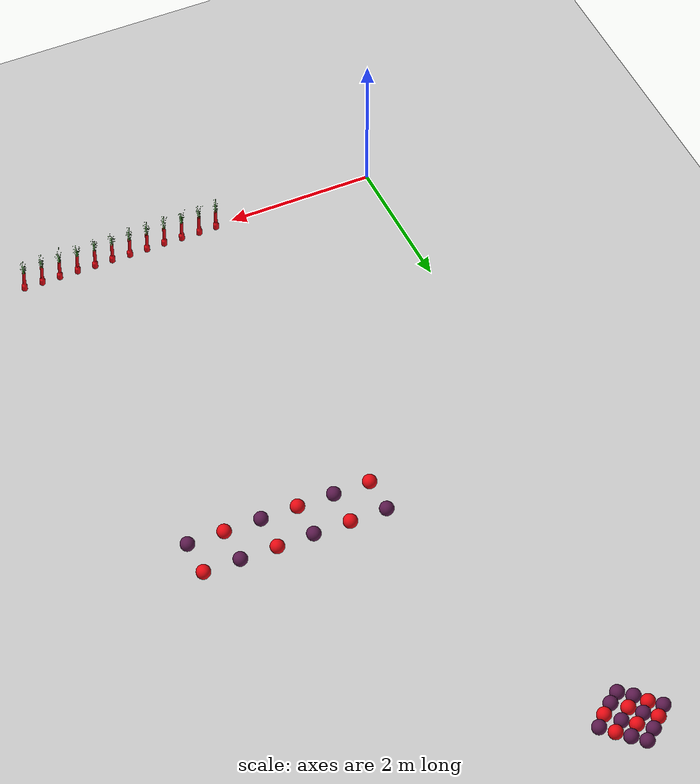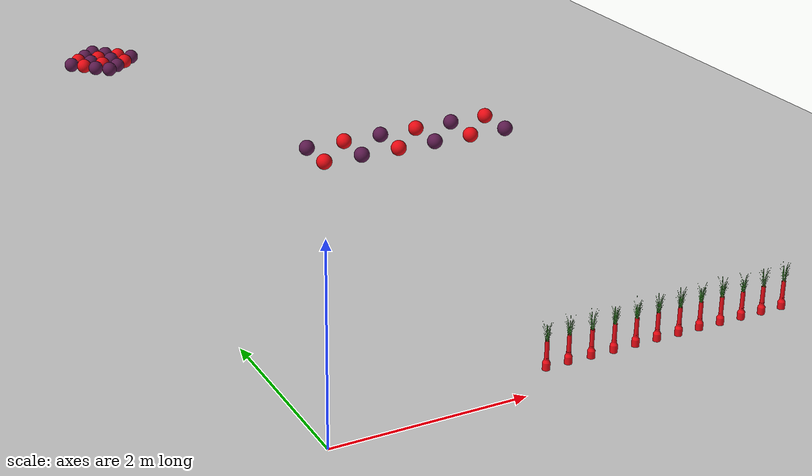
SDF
<sdf version="1.7">
 <world name="default">
  <light name="sun" type="directional">
   <pose>0 0 10 0 -0 0</pose>
   <diffuse>0.8 0.8 0.8 1</diffuse>
   <specular>0.2 0.2 0.2 1</specular>
   <attenuation>
    <range>1000</range>
    <constant>0.9</constant>
    <linear>0.01</linear>
    <quadratic>0.001</quadratic>
   </attenuation>
   <direction>-0.5 0.1 -0.9</direction>
   <spot><inner_angle>0</inner_angle><outer_angle>0</outer_angle><falloff>0</falloff></spot>
  </light>
  <model name="ground_plane">
   <static>1</static>
   <link name="link">
    <collision name="collision">
     <geometry><plane><normal>0 0 1</normal><size>100 100</size></plane></geometry>
     <surface>
      <contact><collide_bitmask>65535</collide_bitmask></contact>
      <friction><ode><mu>100</mu><mu2>50</mu2></ode></friction>
     </surface>
    </collision>
    <visual name="visual">
     <cast_shadows>0</cast_shadows>
     <geometry><plane><normal>0 0 1</normal><size>100 100</size></plane></geometry>
     <material>
      <script><uri>file://media/materials/scripts/gazebo.material</uri><name>Gazebo/Grey</name></script>
     </material>
    </visual>
   </link>
  </model>
  <gravity>0 0 -9.8</gravity>
  <magnetic_field>6e-06 2.3e-05 -4.2e-05</magnetic_field>
  <atmosphere type="adiabatic"/>
  <physics type="ode">
   <max_step_size>0.001</max_step_size>
   <real_time_factor>1</real_time_factor>
   <real_time_update_rate>1000</real_time_update_rate>
  </physics>
  <scene><ambient>0.4 0.4 0.4 1</ambient><background>0.7 0.7 0.7 1</background><shadows>1</shadows></scene>
  <audio><device>default</device></audio>
  <spherical_coordinates>
   <surface_model>EARTH_WGS84</surface_model>
   <latitude_deg>0</latitude_deg>
   <longitude_deg>0</longitude_deg>
   <elevation>0</elevation>
   <heading_deg>0</heading_deg>
  </spherical_coordinates>
  <model name="seed_red">
   <link name="link_1">
    <inertial>
     <mass>1</mass>
     <inertia>
      <ixx>0.166667</ixx>
      <ixy>0</ixy>
      <ixz>0</ixz>
      <iyy>0.166667</iyy>
      <iyz>0</iyz>
      <izz>0.166667</izz>
     </inertia>
    </inertial>
    <visual name="visual">
     <geometry>
      <mesh><uri>/home/entity014/abu2024_ws/src/abu_description/worlds/seed_red.dae</uri><scale>1 1 1</scale></mesh>
     </geometry>
    </visual>
    <collision name="collision">
     <geometry>
      <mesh><uri>/home/entity014/abu2024_ws/src/abu_description/worlds/seed_red.dae</uri><scale>1 1 1</scale></mesh>
     </geometry>
     <surface>
      <friction>
       <ode><mu>1</mu><mu2>1</mu2><fdir1>0 0 0</fdir1><slip1>0</slip1><slip2>0</slip2></ode>
       <torsional>
        <coefficient>1</coefficient>
        <patch_radius>0</patch_radius>
        <surface_radius>0</surface_radius>
        <use_patch_radius>1</use_patch_radius>
        <ode><slip>0</slip></ode>
       </torsional>
      </friction>
      <bounce><restitution_coefficient>0</restitution_coefficient><threshold>1e+06</threshold></bounce>
      <contact>
       <collide_without_contact>0</collide_without_contact>
       <collide_without_contact_bitmask>1</collide_without_contact_bitmask>
       <collide_bitmask>1</collide_bitmask>
       <ode>
        <soft_cfm>0</soft_cfm>
        <soft_erp>0.2</soft_erp>
        <kp>1e+13</kp>
        <kd>1</kd>
        <max_vel>0.01</max_vel>
        <min_depth>0</min_depth>
       </ode>
       <bullet>
        <split_impulse>1</split_impulse>
        <split_impulse_penetration_threshold>-0.01</split_impulse_penetration_threshold>
        <soft_cfm>0</soft_cfm>
        <soft_erp>0.2</soft_erp>
        <kp>1e+13</kp>
        <kd>1</kd>
       </bullet>
      </contact>
     </surface>
    </collision>
   </link>
   <static>0</static>
   <pose>2.30597 0.160395 0.24437 1e-05 -6e-06 -0.006182</pose>
  </model>
  <model name="seed_red_0">
   <link name="link_1">
    <inertial>
     <mass>1</mass>
     <inertia>
      <ixx>0.166667</ixx>
      <ixy>0</ixy>
      <ixz>0</ixz>
      <iyy>0.166667</iyy>
      <iyz>0</iyz>
      <izz>0.166667</izz>
     </inertia>
    </inertial>
    <visual name="visual">
     <geometry>
      <mesh><uri>/home/entity014/abu2024_ws/src/abu_description/worlds/seed_red.dae</uri><scale>1 1 1</scale></mesh>
     </geometry>
    </visual>
    <collision name="collision">
     <geometry>
      <mesh><uri>/home/entity014/abu2024_ws/src/abu_description/worlds/seed_red.dae</uri><scale>1 1 1</scale></mesh>
     </geometry>
     <surface>
      <friction>
       <ode><mu>1</mu><mu2>1</mu2><fdir1>0 0 0</fdir1><slip1>0</slip1><slip2>0</slip2></ode>
       <torsional>
        <coefficient>1</coefficient>
        <patch_radius>0</patch_radius>
        <surface_radius>0</surface_radius>
        <use_patch_radius>1</use_patch_radius>
        <ode><slip>0</slip></ode>
       </torsional>
      </friction>
      <bounce><restitution_coefficient>0</restitution_coefficient><threshold>1e+06</threshold></bounce>
      <contact>
       <collide_without_contact>0</collide_without_contact>
       <collide_without_contact_bitmask>1</collide_without_contact_bitmask>
       <collide_bitmask>1</collide_bitmask>
       <ode>
        <soft_cfm>0</soft_cfm>
        <soft_erp>0.2</soft_erp>
        <kp>1e+13</kp>
        <kd>1</kd>
        <max_vel>0.01</max_vel>
        <min_depth>0</min_depth>
       </ode>
       <bullet>
        <split_impulse>1</split_impulse>
        <split_impulse_penetration_threshold>-0.01</split_impulse_penetration_threshold>
        <soft_cfm>0</soft_cfm>
        <soft_erp>0.2</soft_erp>
        <kp>1e+13</kp>
        <kd>1</kd>
       </bullet>
      </contact>
     </surface>
    </collision>
   </link>
   <static>0</static>
   <pose>2.55267 0.166548 0.244409 0.000556 0.00091 -1.28036</pose>
  </model>
  <model name="seed_red_1">
   <link name="link_1">
    <inertial>
     <mass>1</mass>
     <inertia>
      <ixx>0.166667</ixx>
      <ixy>0</ixy>
      <ixz>0</ixz>
      <iyy>0.166667</iyy>
      <iyz>0</iyz>
      <izz>0.166667</izz>
     </inertia>
    </inertial>
    <visual name="visual">
     <geometry>
      <mesh><uri>/home/entity014/abu2024_ws/src/abu_description/worlds/seed_red.dae</uri><scale>1 1 1</scale></mesh>
     </geometry>
    </visual>
    <collision name="collision">
     <geometry>
      <mesh><uri>/home/entity014/abu2024_ws/src/abu_description/worlds/seed_red.dae</uri><scale>1 1 1</scale></mesh>
     </geometry>
     <surface>
      <friction>
       <ode><mu>1</mu><mu2>1</mu2><fdir1>0 0 0</fdir1><slip1>0</slip1><slip2>0</slip2></ode>
       <torsional>
        <coefficient>1</coefficient>
        <patch_radius>0</patch_radius>
        <surface_radius>0</surface_radius>
        <use_patch_radius>1</use_patch_radius>
        <ode><slip>0</slip></ode>
       </torsional>
      </friction>
      <bounce><restitution_coefficient>0</restitution_coefficient><threshold>1e+06</threshold></bounce>
      <contact>
       <collide_without_contact>0</collide_without_contact>
       <collide_without_contact_bitmask>1</collide_without_contact_bitmask>
       <collide_bitmask>1</collide_bitmask>
       <ode>
        <soft_cfm>0</soft_cfm>
        <soft_erp>0.2</soft_erp>
        <kp>1e+13</kp>
        <kd>1</kd>
        <max_vel>0.01</max_vel>
        <min_depth>0</min_depth>
       </ode>
       <bullet>
        <split_impulse>1</split_impulse>
        <split_impulse_penetration_threshold>-0.01</split_impulse_penetration_threshold>
        <soft_cfm>0</soft_cfm>
        <soft_erp>0.2</soft_erp>
        <kp>1e+13</kp>
        <kd>1</kd>
       </bullet>
      </contact>
     </surface>
    </collision>
   </link>
   <static>0</static>
   <pose>2.80489 0.16348 0.244359 4e-06 1e-06 0.181889</pose>
  </model>
  <model name="seed_red_2">
   <link name="link_1">
    <inertial>
     <mass>1</mass>
     <inertia>
      <ixx>0.166667</ixx>
      <ixy>0</ixy>
      <ixz>0</ixz>
      <iyy>0.166667</iyy>
      <iyz>0</iyz>
      <izz>0.166667</izz>
     </inertia>
    </inertial>
    <visual name="visual">
     <geometry>
      <mesh><uri>/home/entity014/abu2024_ws/src/abu_description/worlds/seed_red.dae</uri><scale>1 1 1</scale></mesh>
     </geometry>
    </visual>
    <collision name="collision">
     <geometry>
      <mesh><uri>/home/entity014/abu2024_ws/src/abu_description/worlds/seed_red.dae</uri><scale>1 1 1</scale></mesh>
     </geometry>
     <surface>
      <friction>
       <ode><mu>1</mu><mu2>1</mu2><fdir1>0 0 0</fdir1><slip1>0</slip1><slip2>0</slip2></ode>
       <torsional>
        <coefficient>1</coefficient>
        <patch_radius>0</patch_radius>
        <surface_radius>0</surface_radius>
        <use_patch_radius>1</use_patch_radius>
        <ode><slip>0</slip></ode>
       </torsional>
      </friction>
      <bounce><restitution_coefficient>0</restitution_coefficient><threshold>1e+06</threshold></bounce>
      <contact>
       <collide_without_contact>0</collide_without_contact>
       <collide_without_contact_bitmask>1</collide_without_contact_bitmask>
       <collide_bitmask>1</collide_bitmask>
       <ode>
        <soft_cfm>0</soft_cfm>
        <soft_erp>0.2</soft_erp>
        <kp>1e+13</kp>
        <kd>1</kd>
        <max_vel>0.01</max_vel>
        <min_depth>0</min_depth>
       </ode>
       <bullet>
        <split_impulse>1</split_impulse>
        <split_impulse_penetration_threshold>-0.01</split_impulse_penetration_threshold>
        <soft_cfm>0</soft_cfm>
        <soft_erp>0.2</soft_erp>
        <kp>1e+13</kp>
        <kd>1</kd>
       </bullet>
      </contact>
     </surface>
    </collision>
   </link>
   <static>0</static>
   <pose>3.05658 0.160248 0.244369 -0 -2e-06 0.02649</pose>
  </model>
  <model name="seed_red_3">
   <link name="link_1">
    <inertial>
     <mass>1</mass>
     <inertia>
      <ixx>0.166667</ixx>
      <ixy>0</ixy>
      <ixz>0</ixz>
      <iyy>0.166667</iyy>
      <iyz>0</iyz>
      <izz>0.166667</izz>
     </inertia>
    </inertial>
    <visual name="visual">
     <geometry>
      <mesh><uri>/home/entity014/abu2024_ws/src/abu_description/worlds/seed_red.dae</uri><scale>1 1 1</scale></mesh>
     </geometry>
    </visual>
    <collision name="collision">
     <geometry>
      <mesh><uri>/home/entity014/abu2024_ws/src/abu_description/worlds/seed_red.dae</uri><scale>1 1 1</scale></mesh>
     </geometry>
     <surface>
      <friction>
       <ode><mu>1</mu><mu2>1</mu2><fdir1>0 0 0</fdir1><slip1>0</slip1><slip2>0</slip2></ode>
       <torsional>
        <coefficient>1</coefficient>
        <patch_radius>0</patch_radius>
        <surface_radius>0</surface_radius>
        <use_patch_radius>1</use_patch_radius>
        <ode><slip>0</slip></ode>
       </torsional>
      </friction>
      <bounce><restitution_coefficient>0</restitution_coefficient><threshold>1e+06</threshold></bounce>
      <contact>
       <collide_without_contact>0</collide_without_contact>
       <collide_without_contact_bitmask>1</collide_without_contact_bitmask>
       <collide_bitmask>1</collide_bitmask>
       <ode>
        <soft_cfm>0</soft_cfm>
        <soft_erp>0.2</soft_erp>
        <kp>1e+13</kp>
        <kd>1</kd>
        <max_vel>0.01</max_vel>
        <min_depth>0</min_depth>
       </ode>
       <bullet>
        <split_impulse>1</split_impulse>
        <split_impulse_penetration_threshold>-0.01</split_impulse_penetration_threshold>
        <soft_cfm>0</soft_cfm>
        <soft_erp>0.2</soft_erp>
        <kp>1e+13</kp>
        <kd>1</kd>
       </bullet>
      </contact>
     </surface>
    </collision>
   </link>
   <static>0</static>
   <pose>3.30914 0.165651 0.244369 0 -2e-06 -0.000402</pose>
  </model>
  <model name="seed_red_4">
   <link name="link_1">
    <inertial>
     <mass>1</mass>
     <inertia>
      <ixx>0.166667</ixx>
      <ixy>0</ixy>
      <ixz>0</ixz>
      <iyy>0.166667</iyy>
      <iyz>0</iyz>
      <izz>0.166667</izz>
     </inertia>
    </inertial>
    <visual name="visual">
     <geometry>
      <mesh><uri>/home/entity014/abu2024_ws/src/abu_description/worlds/seed_red.dae</uri><scale>1 1 1</scale></mesh>
     </geometry>
    </visual>
    <collision name="collision">
     <geometry>
      <mesh><uri>/home/entity014/abu2024_ws/src/abu_description/worlds/seed_red.dae</uri><scale>1 1 1</scale></mesh>
     </geometry>
     <surface>
      <friction>
       <ode><mu>1</mu><mu2>1</mu2><fdir1>0 0 0</fdir1><slip1>0</slip1><slip2>0</slip2></ode>
       <torsional>
        <coefficient>1</coefficient>
        <patch_radius>0</patch_radius>
        <surface_radius>0</surface_radius>
        <use_patch_radius>1</use_patch_radius>
        <ode><slip>0</slip></ode>
       </torsional>
      </friction>
      <bounce><restitution_coefficient>0</restitution_coefficient><threshold>1e+06</threshold></bounce>
      <contact>
       <collide_without_contact>0</collide_without_contact>
       <collide_without_contact_bitmask>1</collide_without_contact_bitmask>
       <collide_bitmask>1</collide_bitmask>
       <ode>
        <soft_cfm>0</soft_cfm>
        <soft_erp>0.2</soft_erp>
        <kp>1e+13</kp>
        <kd>1</kd>
        <max_vel>0.01</max_vel>
        <min_depth>0</min_depth>
       </ode>
       <bullet>
        <split_impulse>1</split_impulse>
        <split_impulse_penetration_threshold>-0.01</split_impulse_penetration_threshold>
        <soft_cfm>0</soft_cfm>
        <soft_erp>0.2</soft_erp>
        <kp>1e+13</kp>
        <kd>1</kd>
       </bullet>
      </contact>
     </surface>
    </collision>
   </link>
   <static>0</static>
   <pose>3.55706 0.165017 0.24437 3e-06 1.8e-05 0.007047</pose>
  </model>
  <model name="seed_red_5">
   <link name="link_1">
    <inertial>
     <mass>1</mass>
     <inertia>
      <ixx>0.166667</ixx>
      <ixy>0</ixy>
      <ixz>0</ixz>
      <iyy>0.166667</iyy>
      <iyz>0</iyz>
      <izz>0.166667</izz>
     </inertia>
    </inertial>
    <visual name="visual">
     <geometry>
      <mesh><uri>/home/entity014/abu2024_ws/src/abu_description/worlds/seed_red.dae</uri><scale>1 1 1</scale></mesh>
     </geometry>
    </visual>
    <collision name="collision">
     <geometry>
      <mesh><uri>/home/entity014/abu2024_ws/src/abu_description/worlds/seed_red.dae</uri><scale>1 1 1</scale></mesh>
     </geometry>
     <surface>
      <friction>
       <ode><mu>1</mu><mu2>1</mu2><fdir1>0 0 0</fdir1><slip1>0</slip1><slip2>0</slip2></ode>
       <torsional>
        <coefficient>1</coefficient>
        <patch_radius>0</patch_radius>
        <surface_radius>0</surface_radius>
        <use_patch_radius>1</use_patch_radius>
        <ode><slip>0</slip></ode>
       </torsional>
      </friction>
      <bounce><restitution_coefficient>0</restitution_coefficient><threshold>1e+06</threshold></bounce>
      <contact>
       <collide_without_contact>0</collide_without_contact>
       <collide_without_contact_bitmask>1</collide_without_contact_bitmask>
       <collide_bitmask>1</collide_bitmask>
       <ode>
        <soft_cfm>0</soft_cfm>
        <soft_erp>0.2</soft_erp>
        <kp>1e+13</kp>
        <kd>1</kd>
        <max_vel>0.01</max_vel>
        <min_depth>0</min_depth>
       </ode>
       <bullet>
        <split_impulse>1</split_impulse>
        <split_impulse_penetration_threshold>-0.01</split_impulse_penetration_threshold>
        <soft_cfm>0</soft_cfm>
        <soft_erp>0.2</soft_erp>
        <kp>1e+13</kp>
        <kd>1</kd>
       </bullet>
      </contact>
     </surface>
    </collision>
   </link>
   <static>0</static>
   <pose>3.80696 0.160767 0.244369 6e-06 -5e-06 -0.002717</pose>
  </model>
  <model name="seed_red_6">
   <link name="link_1">
    <inertial>
     <mass>1</mass>
     <inertia>
      <ixx>0.166667</ixx>
      <ixy>0</ixy>
      <ixz>0</ixz>
      <iyy>0.166667</iyy>
      <iyz>0</iyz>
      <izz>0.166667</izz>
     </inertia>
    </inertial>
    <visual name="visual">
     <geometry>
      <mesh><uri>/home/entity014/abu2024_ws/src/abu_description/worlds/seed_red.dae</uri><scale>1 1 1</scale></mesh>
     </geometry>
    </visual>
    <collision name="collision">
     <geometry>
      <mesh><uri>/home/entity014/abu2024_ws/src/abu_description/worlds/seed_red.dae</uri><scale>1 1 1</scale></mesh>
     </geometry>
     <surface>
      <friction>
       <ode><mu>1</mu><mu2>1</mu2><fdir1>0 0 0</fdir1><slip1>0</slip1><slip2>0</slip2></ode>
       <torsional>
        <coefficient>1</coefficient>
        <patch_radius>0</patch_radius>
        <surface_radius>0</surface_radius>
        <use_patch_radius>1</use_patch_radius>
        <ode><slip>0</slip></ode>
       </torsional>
      </friction>
      <bounce><restitution_coefficient>0</restitution_coefficient><threshold>1e+06</threshold></bounce>
      <contact>
       <collide_without_contact>0</collide_without_contact>
       <collide_without_contact_bitmask>1</collide_without_contact_bitmask>
       <collide_bitmask>1</collide_bitmask>
       <ode>
        <soft_cfm>0</soft_cfm>
        <soft_erp>0.2</soft_erp>
        <kp>1e+13</kp>
        <kd>1</kd>
        <max_vel>0.01</max_vel>
        <min_depth>0</min_depth>
       </ode>
       <bullet>
        <split_impulse>1</split_impulse>
        <split_impulse_penetration_threshold>-0.01</split_impulse_penetration_threshold>
        <soft_cfm>0</soft_cfm>
        <soft_erp>0.2</soft_erp>
        <kp>1e+13</kp>
        <kd>1</kd>
       </bullet>
      </contact>
     </surface>
    </collision>
   </link>
   <static>0</static>
   <pose>4.0561 0.163956 0.244369 5e-06 -7e-06 -0.03263</pose>
  </model>
  <model name="seed_red_7">
   <link name="link_1">
    <inertial>
     <mass>1</mass>
     <inertia>
      <ixx>0.166667</ixx>
      <ixy>0</ixy>
      <ixz>0</ixz>
      <iyy>0.166667</iyy>
      <iyz>0</iyz>
      <izz>0.166667</izz>
     </inertia>
    </inertial>
    <visual name="visual">
     <geometry>
      <mesh><uri>/home/entity014/abu2024_ws/src/abu_description/worlds/seed_red.dae</uri><scale>1 1 1</scale></mesh>
     </geometry>
    </visual>
    <collision name="collision">
     <geometry>
      <mesh><uri>/home/entity014/abu2024_ws/src/abu_description/worlds/seed_red.dae</uri><scale>1 1 1</scale></mesh>
     </geometry>
     <surface>
      <friction>
       <ode><mu>1</mu><mu2>1</mu2><fdir1>0 0 0</fdir1><slip1>0</slip1><slip2>0</slip2></ode>
       <torsional>
        <coefficient>1</coefficient>
        <patch_radius>0</patch_radius>
        <surface_radius>0</surface_radius>
        <use_patch_radius>1</use_patch_radius>
        <ode><slip>0</slip></ode>
       </torsional>
      </friction>
      <bounce><restitution_coefficient>0</restitution_coefficient><threshold>1e+06</threshold></bounce>
      <contact>
       <collide_without_contact>0</collide_without_contact>
       <collide_without_contact_bitmask>1</collide_without_contact_bitmask>
       <collide_bitmask>1</collide_bitmask>
       <ode>
        <soft_cfm>0</soft_cfm>
        <soft_erp>0.2</soft_erp>
        <kp>1e+13</kp>
        <kd>1</kd>
        <max_vel>0.01</max_vel>
        <min_depth>0</min_depth>
       </ode>
       <bullet>
        <split_impulse>1</split_impulse>
        <split_impulse_penetration_threshold>-0.01</split_impulse_penetration_threshold>
        <soft_cfm>0</soft_cfm>
        <soft_erp>0.2</soft_erp>
        <kp>1e+13</kp>
        <kd>1</kd>
       </bullet>
      </contact>
     </surface>
    </collision>
   </link>
   <static>0</static>
   <pose>4.30494 0.160936 0.244369 1e-06 0 -0.020611</pose>
  </model>
  <model name="seed_red_8">
   <link name="link_1">
    <inertial>
     <mass>1</mass>
     <inertia>
      <ixx>0.166667</ixx>
      <ixy>0</ixy>
      <ixz>0</ixz>
      <iyy>0.166667</iyy>
      <iyz>0</iyz>
      <izz>0.166667</izz>
     </inertia>
    </inertial>
    <visual name="visual">
     <geometry>
      <mesh><uri>/home/entity014/abu2024_ws/src/abu_description/worlds/seed_red.dae</uri><scale>1 1 1</scale></mesh>
     </geometry>
    </visual>
    <collision name="collision">
     <geometry>
      <mesh><uri>/home/entity014/abu2024_ws/src/abu_description/worlds/seed_red.dae</uri><scale>1 1 1</scale></mesh>
     </geometry>
     <surface>
      <friction>
       <ode><mu>1</mu><mu2>1</mu2><fdir1>0 0 0</fdir1><slip1>0</slip1><slip2>0</slip2></ode>
       <torsional>
        <coefficient>1</coefficient>
        <patch_radius>0</patch_radius>
        <surface_radius>0</surface_radius>
        <use_patch_radius>1</use_patch_radius>
        <ode><slip>0</slip></ode>
       </torsional>
      </friction>
      <bounce><restitution_coefficient>0</restitution_coefficient><threshold>1e+06</threshold></bounce>
      <contact>
       <collide_without_contact>0</collide_without_contact>
       <collide_without_contact_bitmask>1</collide_without_contact_bitmask>
       <collide_bitmask>1</collide_bitmask>
       <ode>
        <soft_cfm>0</soft_cfm>
        <soft_erp>0.2</soft_erp>
        <kp>1e+13</kp>
        <kd>1</kd>
        <max_vel>0.01</max_vel>
        <min_depth>0</min_depth>
       </ode>
       <bullet>
        <split_impulse>1</split_impulse>
        <split_impulse_penetration_threshold>-0.01</split_impulse_penetration_threshold>
        <soft_cfm>0</soft_cfm>
        <soft_erp>0.2</soft_erp>
        <kp>1e+13</kp>
        <kd>1</kd>
       </bullet>
      </contact>
     </surface>
    </collision>
   </link>
   <static>0</static>
   <pose>4.5602 0.162003 0.24437 -9e-06 -7e-06 0.000209</pose>
  </model>
  <model name="seed_red_9">
   <link name="link_1">
    <inertial>
     <mass>1</mass>
     <inertia>
      <ixx>0.166667</ixx>
      <ixy>0</ixy>
      <ixz>0</ixz>
      <iyy>0.166667</iyy>
      <iyz>0</iyz>
      <izz>0.166667</izz>
     </inertia>
    </inertial>
    <visual name="visual">
     <geometry>
      <mesh><uri>/home/entity014/abu2024_ws/src/abu_description/worlds/seed_red.dae</uri><scale>1 1 1</scale></mesh>
     </geometry>
    </visual>
    <collision name="collision">
     <geometry>
      <mesh><uri>/home/entity014/abu2024_ws/src/abu_description/worlds/seed_red.dae</uri><scale>1 1 1</scale></mesh>
     </geometry>
     <surface>
      <friction>
       <ode><mu>1</mu><mu2>1</mu2><fdir1>0 0 0</fdir1><slip1>0</slip1><slip2>0</slip2></ode>
       <torsional>
        <coefficient>1</coefficient>
        <patch_radius>0</patch_radius>
        <surface_radius>0</surface_radius>
        <use_patch_radius>1</use_patch_radius>
        <ode><slip>0</slip></ode>
       </torsional>
      </friction>
      <bounce><restitution_coefficient>0</restitution_coefficient><threshold>1e+06</threshold></bounce>
      <contact>
       <collide_without_contact>0</collide_without_contact>
       <collide_without_contact_bitmask>1</collide_without_contact_bitmask>
       <collide_bitmask>1</collide_bitmask>
       <ode>
        <soft_cfm>0</soft_cfm>
        <soft_erp>0.2</soft_erp>
        <kp>1e+13</kp>
        <kd>1</kd>
        <max_vel>0.01</max_vel>
        <min_depth>0</min_depth>
       </ode>
       <bullet>
        <split_impulse>1</split_impulse>
        <split_impulse_penetration_threshold>-0.01</split_impulse_penetration_threshold>
        <soft_cfm>0</soft_cfm>
        <soft_erp>0.2</soft_erp>
        <kp>1e+13</kp>
        <kd>1</kd>
       </bullet>
      </contact>
     </surface>
    </collision>
   </link>
   <static>0</static>
   <pose>4.80888 0.160134 0.244369 6e-06 -8e-06 0.116256</pose>
  </model>
  <model name="seed_red_10">
   <link name="link_1">
    <inertial>
     <mass>1</mass>
     <inertia>
      <ixx>0.166667</ixx>
      <ixy>0</ixy>
      <ixz>0</ixz>
      <iyy>0.166667</iyy>
      <iyz>0</iyz>
      <izz>0.166667</izz>
     </inertia>
    </inertial>
    <visual name="visual">
     <geometry>
      <mesh><uri>/home/entity014/abu2024_ws/src/abu_description/worlds/seed_red.dae</uri><scale>1 1 1</scale></mesh>
     </geometry>
    </visual>
    <collision name="collision">
     <geometry>
      <mesh><uri>/home/entity014/abu2024_ws/src/abu_description/worlds/seed_red.dae</uri><scale>1 1 1</scale></mesh>
     </geometry>
     <surface>
      <friction>
       <ode><mu>1</mu><mu2>1</mu2><fdir1>0 0 0</fdir1><slip1>0</slip1><slip2>0</slip2></ode>
       <torsional>
        <coefficient>1</coefficient>
        <patch_radius>0</patch_radius>
        <surface_radius>0</surface_radius>
        <use_patch_radius>1</use_patch_radius>
        <ode><slip>0</slip></ode>
       </torsional>
      </friction>
      <bounce><restitution_coefficient>0</restitution_coefficient><threshold>1e+06</threshold></bounce>
      <contact>
       <collide_without_contact>0</collide_without_contact>
       <collide_without_contact_bitmask>1</collide_without_contact_bitmask>
       <collide_bitmask>1</collide_bitmask>
       <ode>
        <soft_cfm>0</soft_cfm>
        <soft_erp>0.2</soft_erp>
        <kp>1e+13</kp>
        <kd>1</kd>
        <max_vel>0.01</max_vel>
        <min_depth>0</min_depth>
       </ode>
       <bullet>
        <split_impulse>1</split_impulse>
        <split_impulse_penetration_threshold>-0.01</split_impulse_penetration_threshold>
        <soft_cfm>0</soft_cfm>
        <soft_erp>0.2</soft_erp>
        <kp>1e+13</kp>
        <kd>1</kd>
       </bullet>
      </contact>
     </surface>
    </collision>
   </link>
   <static>0</static>
   <pose>5.06177 0.161648 0.244369 -2e-06 -1e-06 0.173481</pose>
  </model>
  <model name="ball_empty">
   <link name="link_1">
    <inertial>
     <mass>1</mass>
     <inertia>
      <ixx>0.166667</ixx>
      <ixy>0</ixy>
      <ixz>0</ixz>
      <iyy>0.166667</iyy>
      <iyz>0</iyz>
      <izz>0.166667</izz>
     </inertia>
    </inertial>
    <visual name="visual">
     <geometry>
      <mesh>
       <uri>/home/entity014/abu2024_ws/src/abu_description/worlds/ball_empty.dae</uri>
       <scale>1 1 1</scale>
      </mesh>
     </geometry>
    </visual>
    <collision name="collision">
     <geometry>
      <mesh>
       <uri>/home/entity014/abu2024_ws/src/abu_description/worlds/ball_empty.dae</uri>
       <scale>1 1 1</scale>
      </mesh>
     </geometry>
     <surface>
      <friction>
       <ode><mu>1</mu><mu2>1</mu2><fdir1>0 0 0</fdir1><slip1>0</slip1><slip2>0</slip2></ode>
       <torsional>
        <coefficient>1</coefficient>
        <patch_radius>0</patch_radius>
        <surface_radius>0</surface_radius>
        <use_patch_radius>1</use_patch_radius>
        <ode><slip>0</slip></ode>
       </torsional>
      </friction>
      <bounce><restitution_coefficient>0</restitution_coefficient><threshold>1e+06</threshold></bounce>
      <contact>
       <collide_without_contact>0</collide_without_contact>
       <collide_without_contact_bitmask>1</collide_without_contact_bitmask>
       <collide_bitmask>1</collide_bitmask>
       <ode>
        <soft_cfm>0</soft_cfm>
        <soft_erp>0.2</soft_erp>
        <kp>1e+13</kp>
        <kd>1</kd>
        <max_vel>0.01</max_vel>
        <min_depth>0</min_depth>
       </ode>
       <bullet>
        <split_impulse>1</split_impulse>
        <split_impulse_penetration_threshold>-0.01</split_impulse_penetration_threshold>
        <soft_cfm>0</soft_cfm>
        <soft_erp>0.2</soft_erp>
        <kp>1e+13</kp>
        <kd>1</kd>
       </bullet>
      </contact>
     </surface>
    </collision>
   </link>
   <static>0</static>
   <pose>2.43205 5.79343 0.302534 0.214684 0.294643 0.005747</pose>
  </model>
  <model name="ball_empty_clone">
   <link name="link_1">
    <inertial>
     <mass>1</mass>
     <inertia>
      <ixx>0.166667</ixx>
      <ixy>0</ixy>
      <ixz>0</ixz>
      <iyy>0.166667</iyy>
      <iyz>0</iyz>
      <izz>0.166667</izz>
     </inertia>
    </inertial>
    <visual name="visual">
     <geometry>
      <mesh>
       <uri>/home/entity014/abu2024_ws/src/abu_description/worlds/ball_empty.dae</uri>
       <scale>1 1 1</scale>
      </mesh>
     </geometry>
    </visual>
    <collision name="collision">
     <geometry>
      <mesh>
       <uri>/home/entity014/abu2024_ws/src/abu_description/worlds/ball_empty.dae</uri>
       <scale>1 1 1</scale>
      </mesh>
     </geometry>
     <surface>
      <friction>
       <ode><mu>1</mu><mu2>1</mu2><fdir1>0 0 0</fdir1><slip1>0</slip1><slip2>0</slip2></ode>
       <torsional>
        <coefficient>1</coefficient>
        <patch_radius>0</patch_radius>
        <surface_radius>0</surface_radius>
        <use_patch_radius>1</use_patch_radius>
        <ode><slip>0</slip></ode>
       </torsional>
      </friction>
      <bounce><restitution_coefficient>0</restitution_coefficient><threshold>1e+06</threshold></bounce>
      <contact>
       <collide_without_contact>0</collide_without_contact>
       <collide_without_contact_bitmask>1</collide_without_contact_bitmask>
       <collide_bitmask>1</collide_bitmask>
       <ode>
        <soft_cfm>0</soft_cfm>
        <soft_erp>0.2</soft_erp>
        <kp>1e+13</kp>
        <kd>1</kd>
        <max_vel>0.01</max_vel>
        <min_depth>0</min_depth>
       </ode>
       <bullet>
        <split_impulse>1</split_impulse>
        <split_impulse_penetration_threshold>-0.01</split_impulse_penetration_threshold>
        <soft_cfm>0</soft_cfm>
        <soft_erp>0.2</soft_erp>
        <kp>1e+13</kp>
        <kd>1</kd>
       </bullet>
      </contact>
     </surface>
    </collision>
   </link>
   <static>0</static>
   <pose>2.93186 5.29326 0.302543 -0.06972 0.098857 -0.036473</pose>
  </model>
  <model name="ball_empty_clone_0">
   <link name="link_1">
    <inertial>
     <mass>1</mass>
     <inertia>
      <ixx>0.166667</ixx>
      <ixy>0</ixy>
      <ixz>0</ixz>
      <iyy>0.166667</iyy>
      <iyz>0</iyz>
      <izz>0.166667</izz>
     </inertia>
    </inertial>
    <visual name="visual">
     <geometry>
      <mesh>
       <uri>/home/entity014/abu2024_ws/src/abu_description/worlds/ball_empty.dae</uri>
       <scale>1 1 1</scale>
      </mesh>
     </geometry>
    </visual>
    <collision name="collision">
     <geometry>
      <mesh>
       <uri>/home/entity014/abu2024_ws/src/abu_description/worlds/ball_empty.dae</uri>
       <scale>1 1 1</scale>
      </mesh>
     </geometry>
     <surface>
      <friction>
       <ode><mu>1</mu><mu2>1</mu2><fdir1>0 0 0</fdir1><slip1>0</slip1><slip2>0</slip2></ode>
       <torsional>
        <coefficient>1</coefficient>
        <patch_radius>0</patch_radius>
        <surface_radius>0</surface_radius>
        <use_patch_radius>1</use_patch_radius>
        <ode><slip>0</slip></ode>
       </torsional>
      </friction>
      <bounce><restitution_coefficient>0</restitution_coefficient><threshold>1e+06</threshold></bounce>
      <contact>
       <collide_without_contact>0</collide_without_contact>
       <collide_without_contact_bitmask>1</collide_without_contact_bitmask>
       <collide_bitmask>1</collide_bitmask>
       <ode>
        <soft_cfm>0</soft_cfm>
        <soft_erp>0.2</soft_erp>
        <kp>1e+13</kp>
        <kd>1</kd>
        <max_vel>0.01</max_vel>
        <min_depth>0</min_depth>
       </ode>
       <bullet>
        <split_impulse>1</split_impulse>
        <split_impulse_penetration_threshold>-0.01</split_impulse_penetration_threshold>
        <soft_cfm>0</soft_cfm>
        <soft_erp>0.2</soft_erp>
        <kp>1e+13</kp>
        <kd>1</kd>
       </bullet>
      </contact>
     </surface>
    </collision>
   </link>
   <static>0</static>
   <pose>3.43449 5.7922 0.302583 -0.16654 -0.252537 0.165302</pose>
  </model>
  <model name="ball_empty_clone_1">
   <link name="link_1">
    <inertial>
     <mass>1</mass>
     <inertia>
      <ixx>0.166667</ixx>
      <ixy>0</ixy>
      <ixz>0</ixz>
      <iyy>0.166667</iyy>
      <iyz>0</iyz>
      <izz>0.166667</izz>
     </inertia>
    </inertial>
    <visual name="visual">
     <geometry>
      <mesh>
       <uri>/home/entity014/abu2024_ws/src/abu_description/worlds/ball_empty.dae</uri>
       <scale>1 1 1</scale>
      </mesh>
     </geometry>
    </visual>
    <collision name="collision">
     <geometry>
      <mesh>
       <uri>/home/entity014/abu2024_ws/src/abu_description/worlds/ball_empty.dae</uri>
       <scale>1 1 1</scale>
      </mesh>
     </geometry>
     <surface>
      <friction>
       <ode><mu>1</mu><mu2>1</mu2><fdir1>0 0 0</fdir1><slip1>0</slip1><slip2>0</slip2></ode>
       <torsional>
        <coefficient>1</coefficient>
        <patch_radius>0</patch_radius>
        <surface_radius>0</surface_radius>
        <use_patch_radius>1</use_patch_radius>
        <ode><slip>0</slip></ode>
       </torsional>
      </friction>
      <bounce><restitution_coefficient>0</restitution_coefficient><threshold>1e+06</threshold></bounce>
      <contact>
       <collide_without_contact>0</collide_without_contact>
       <collide_without_contact_bitmask>1</collide_without_contact_bitmask>
       <collide_bitmask>1</collide_bitmask>
       <ode>
        <soft_cfm>0</soft_cfm>
        <soft_erp>0.2</soft_erp>
        <kp>1e+13</kp>
        <kd>1</kd>
        <max_vel>0.01</max_vel>
        <min_depth>0</min_depth>
       </ode>
       <bullet>
        <split_impulse>1</split_impulse>
        <split_impulse_penetration_threshold>-0.01</split_impulse_penetration_threshold>
        <soft_cfm>0</soft_cfm>
        <soft_erp>0.2</soft_erp>
        <kp>1e+13</kp>
        <kd>1</kd>
       </bullet>
      </contact>
     </surface>
    </collision>
   </link>
   <static>0</static>
   <pose>3.93208 5.29338 0.302509 0.660181 0.421151 0.132481</pose>
  </model>
  <model name="ball_empty_clone_2">
   <link name="link_1">
    <inertial>
     <mass>1</mass>
     <inertia>
      <ixx>0.166667</ixx>
      <ixy>0</ixy>
      <ixz>0</ixz>
      <iyy>0.166667</iyy>
      <iyz>0</iyz>
      <izz>0.166667</izz>
     </inertia>
    </inertial>
    <visual name="visual">
     <geometry>
      <mesh>
       <uri>/home/entity014/abu2024_ws/src/abu_description/worlds/ball_empty.dae</uri>
       <scale>1 1 1</scale>
      </mesh>
     </geometry>
    </visual>
    <collision name="collision">
     <geometry>
      <mesh>
       <uri>/home/entity014/abu2024_ws/src/abu_description/worlds/ball_empty.dae</uri>
       <scale>1 1 1</scale>
      </mesh>
     </geometry>
     <surface>
      <friction>
       <ode><mu>1</mu><mu2>1</mu2><fdir1>0 0 0</fdir1><slip1>0</slip1><slip2>0</slip2></ode>
       <torsional>
        <coefficient>1</coefficient>
        <patch_radius>0</patch_radius>
        <surface_radius>0</surface_radius>
        <use_patch_radius>1</use_patch_radius>
        <ode><slip>0</slip></ode>
       </torsional>
      </friction>
      <bounce><restitution_coefficient>0</restitution_coefficient><threshold>1e+06</threshold></bounce>
      <contact>
       <collide_without_contact>0</collide_without_contact>
       <collide_without_contact_bitmask>1</collide_without_contact_bitmask>
       <collide_bitmask>1</collide_bitmask>
       <ode>
        <soft_cfm>0</soft_cfm>
        <soft_erp>0.2</soft_erp>
        <kp>1e+13</kp>
        <kd>1</kd>
        <max_vel>0.01</max_vel>
        <min_depth>0</min_depth>
       </ode>
       <bullet>
        <split_impulse>1</split_impulse>
        <split_impulse_penetration_threshold>-0.01</split_impulse_penetration_threshold>
        <soft_cfm>0</soft_cfm>
        <soft_erp>0.2</soft_erp>
        <kp>1e+13</kp>
        <kd>1</kd>
       </bullet>
      </contact>
     </surface>
    </collision>
   </link>
   <static>0</static>
   <pose>4.43389 5.7914 0.302505 0.911798 0.178377 0.307818</pose>
  </model>
  <model name="ball_empty_clone_3">
   <link name="link_1">
    <inertial>
     <mass>1</mass>
     <inertia>
      <ixx>0.166667</ixx>
      <ixy>0</ixy>
      <ixz>0</ixz>
      <iyy>0.166667</iyy>
      <iyz>0</iyz>
      <izz>0.166667</izz>
     </inertia>
    </inertial>
    <visual name="visual">
     <geometry>
      <mesh>
       <uri>/home/entity014/abu2024_ws/src/abu_description/worlds/ball_empty.dae</uri>
       <scale>1 1 1</scale>
      </mesh>
     </geometry>
    </visual>
    <collision name="collision">
     <geometry>
      <mesh>
       <uri>/home/entity014/abu2024_ws/src/abu_description/worlds/ball_empty.dae</uri>
       <scale>1 1 1</scale>
      </mesh>
     </geometry>
     <surface>
      <friction>
       <ode><mu>1</mu><mu2>1</mu2><fdir1>0 0 0</fdir1><slip1>0</slip1><slip2>0</slip2></ode>
       <torsional>
        <coefficient>1</coefficient>
        <patch_radius>0</patch_radius>
        <surface_radius>0</surface_radius>
        <use_patch_radius>1</use_patch_radius>
        <ode><slip>0</slip></ode>
       </torsional>
      </friction>
      <bounce><restitution_coefficient>0</restitution_coefficient><threshold>1e+06</threshold></bounce>
      <contact>
       <collide_without_contact>0</collide_without_contact>
       <collide_without_contact_bitmask>1</collide_without_contact_bitmask>
       <collide_bitmask>1</collide_bitmask>
       <ode>
        <soft_cfm>0</soft_cfm>
        <soft_erp>0.2</soft_erp>
        <kp>1e+13</kp>
        <kd>1</kd>
        <max_vel>0.01</max_vel>
        <min_depth>0</min_depth>
       </ode>
       <bullet>
        <split_impulse>1</split_impulse>
        <split_impulse_penetration_threshold>-0.01</split_impulse_penetration_threshold>
        <soft_cfm>0</soft_cfm>
        <soft_erp>0.2</soft_erp>
        <kp>1e+13</kp>
        <kd>1</kd>
       </bullet>
      </contact>
     </surface>
    </collision>
   </link>
   <static>0</static>
   <pose>4.9317 5.29217 0.302545 0.11231 0.167966 -0.116638</pose>
  </model>
  <model name="ball_red">
   <link name="link_1">
    <inertial>
     <mass>1</mass>
     <inertia>
      <ixx>0.166667</ixx>
      <ixy>0</ixy>
      <ixz>0</ixz>
      <iyy>0.166667</iyy>
      <iyz>0</iyz>
      <izz>0.166667</izz>
     </inertia>
    </inertial>
    <visual name="visual">
     <geometry>
      <mesh><uri>/home/entity014/abu2024_ws/src/abu_description/worlds/ball_red.dae</uri><scale>1 1 1</scale></mesh>
     </geometry>
    </visual>
    <collision name="collision">
     <geometry>
      <mesh><uri>/home/entity014/abu2024_ws/src/abu_description/worlds/ball_red.dae</uri><scale>1 1 1</scale></mesh>
     </geometry>
     <surface>
      <friction>
       <ode><mu>1</mu><mu2>1</mu2><fdir1>0 0 0</fdir1><slip1>0</slip1><slip2>0</slip2></ode>
       <torsional>
        <coefficient>1</coefficient>
        <patch_radius>0</patch_radius>
        <surface_radius>0</surface_radius>
        <use_patch_radius>1</use_patch_radius>
        <ode><slip>0</slip></ode>
       </torsional>
      </friction>
      <bounce><restitution_coefficient>0</restitution_coefficient><threshold>1e+06</threshold></bounce>
      <contact>
       <collide_without_contact>0</collide_without_contact>
       <collide_without_contact_bitmask>1</collide_without_contact_bitmask>
       <collide_bitmask>1</collide_bitmask>
       <ode>
        <soft_cfm>0</soft_cfm>
        <soft_erp>0.2</soft_erp>
        <kp>1e+13</kp>
        <kd>1</kd>
        <max_vel>0.01</max_vel>
        <min_depth>0</min_depth>
       </ode>
       <bullet>
        <split_impulse>1</split_impulse>
        <split_impulse_penetration_threshold>-0.01</split_impulse_penetration_threshold>
        <soft_cfm>0</soft_cfm>
        <soft_erp>0.2</soft_erp>
        <kp>1e+13</kp>
        <kd>1</kd>
       </bullet>
      </contact>
     </surface>
    </collision>
   </link>
   <static>0</static>
   <pose>2.43399 5.29357 0.302553 -0.014667 -0.125477 0.657178</pose>
  </model>
  <model name="ball_red_0">
   <link name="link_1">
    <inertial>
     <mass>1</mass>
     <inertia>
      <ixx>0.166667</ixx>
      <ixy>0</ixy>
      <ixz>0</ixz>
      <iyy>0.166667</iyy>
      <iyz>0</iyz>
      <izz>0.166667</izz>
     </inertia>
    </inertial>
    <visual name="visual">
     <geometry>
      <mesh><uri>/home/entity014/abu2024_ws/src/abu_description/worlds/ball_red.dae</uri><scale>1 1 1</scale></mesh>
     </geometry>
    </visual>
    <collision name="collision">
     <geometry>
      <mesh><uri>/home/entity014/abu2024_ws/src/abu_description/worlds/ball_red.dae</uri><scale>1 1 1</scale></mesh>
     </geometry>
     <surface>
      <friction>
       <ode><mu>1</mu><mu2>1</mu2><fdir1>0 0 0</fdir1><slip1>0</slip1><slip2>0</slip2></ode>
       <torsional>
        <coefficient>1</coefficient>
        <patch_radius>0</patch_radius>
        <surface_radius>0</surface_radius>
        <use_patch_radius>1</use_patch_radius>
        <ode><slip>0</slip></ode>
       </torsional>
      </friction>
      <bounce><restitution_coefficient>0</restitution_coefficient><threshold>1e+06</threshold></bounce>
      <contact>
       <collide_without_contact>0</collide_without_contact>
       <collide_without_contact_bitmask>1</collide_without_contact_bitmask>
       <collide_bitmask>1</collide_bitmask>
       <ode>
        <soft_cfm>0</soft_cfm>
        <soft_erp>0.2</soft_erp>
        <kp>1e+13</kp>
        <kd>1</kd>
        <max_vel>0.01</max_vel>
        <min_depth>0</min_depth>
       </ode>
       <bullet>
        <split_impulse>1</split_impulse>
        <split_impulse_penetration_threshold>-0.01</split_impulse_penetration_threshold>
        <soft_cfm>0</soft_cfm>
        <soft_erp>0.2</soft_erp>
        <kp>1e+13</kp>
        <kd>1</kd>
       </bullet>
      </contact>
     </surface>
    </collision>
   </link>
   <static>0</static>
   <pose>3.4319 5.29352 0.302576 0.065241 0.113249 -0.014275</pose>
  </model>
  <model name="ball_red_1">
   <link name="link_1">
    <inertial>
     <mass>1</mass>
     <inertia>
      <ixx>0.166667</ixx>
      <ixy>0</ixy>
      <ixz>0</ixz>
      <iyy>0.166667</iyy>
      <iyz>0</iyz>
      <izz>0.166667</izz>
     </inertia>
    </inertial>
    <visual name="visual">
     <geometry>
      <mesh><uri>/home/entity014/abu2024_ws/src/abu_description/worlds/ball_red.dae</uri><scale>1 1 1</scale></mesh>
     </geometry>
    </visual>
    <collision name="collision">
     <geometry>
      <mesh><uri>/home/entity014/abu2024_ws/src/abu_description/worlds/ball_red.dae</uri><scale>1 1 1</scale></mesh>
     </geometry>
     <surface>
      <friction>
       <ode><mu>1</mu><mu2>1</mu2><fdir1>0 0 0</fdir1><slip1>0</slip1><slip2>0</slip2></ode>
       <torsional>
        <coefficient>1</coefficient>
        <patch_radius>0</patch_radius>
        <surface_radius>0</surface_radius>
        <use_patch_radius>1</use_patch_radius>
        <ode><slip>0</slip></ode>
       </torsional>
      </friction>
      <bounce><restitution_coefficient>0</restitution_coefficient><threshold>1e+06</threshold></bounce>
      <contact>
       <collide_without_contact>0</collide_without_contact>
       <collide_without_contact_bitmask>1</collide_without_contact_bitmask>
       <collide_bitmask>1</collide_bitmask>
       <ode>
        <soft_cfm>0</soft_cfm>
        <soft_erp>0.2</soft_erp>
        <kp>1e+13</kp>
        <kd>1</kd>
        <max_vel>0.01</max_vel>
        <min_depth>0</min_depth>
       </ode>
       <bullet>
        <split_impulse>1</split_impulse>
        <split_impulse_penetration_threshold>-0.01</split_impulse_penetration_threshold>
        <soft_cfm>0</soft_cfm>
        <soft_erp>0.2</soft_erp>
        <kp>1e+13</kp>
        <kd>1</kd>
       </bullet>
      </contact>
     </surface>
    </collision>
   </link>
   <static>0</static>
   <pose>2.93359 5.79364 0.302534 -0.079421 0.091164 -0.015579</pose>
  </model>
  <model name="ball_red_2">
   <link name="link_1">
    <inertial>
     <mass>1</mass>
     <inertia>
      <ixx>0.166667</ixx>
      <ixy>0</ixy>
      <ixz>0</ixz>
      <iyy>0.166667</iyy>
      <iyz>0</iyz>
      <izz>0.166667</izz>
     </inertia>
    </inertial>
    <visual name="visual">
     <geometry>
      <mesh><uri>/home/entity014/abu2024_ws/src/abu_description/worlds/ball_red.dae</uri><scale>1 1 1</scale></mesh>
     </geometry>
    </visual>
    <collision name="collision">
     <geometry>
      <mesh><uri>/home/entity014/abu2024_ws/src/abu_description/worlds/ball_red.dae</uri><scale>1 1 1</scale></mesh>
     </geometry>
     <surface>
      <friction>
       <ode><mu>1</mu><mu2>1</mu2><fdir1>0 0 0</fdir1><slip1>0</slip1><slip2>0</slip2></ode>
       <torsional>
        <coefficient>1</coefficient>
        <patch_radius>0</patch_radius>
        <surface_radius>0</surface_radius>
        <use_patch_radius>1</use_patch_radius>
        <ode><slip>0</slip></ode>
       </torsional>
      </friction>
      <bounce><restitution_coefficient>0</restitution_coefficient><threshold>1e+06</threshold></bounce>
      <contact>
       <collide_without_contact>0</collide_without_contact>
       <collide_without_contact_bitmask>1</collide_without_contact_bitmask>
       <collide_bitmask>1</collide_bitmask>
       <ode>
        <soft_cfm>0</soft_cfm>
        <soft_erp>0.2</soft_erp>
        <kp>1e+13</kp>
        <kd>1</kd>
        <max_vel>0.01</max_vel>
        <min_depth>0</min_depth>
       </ode>
       <bullet>
        <split_impulse>1</split_impulse>
        <split_impulse_penetration_threshold>-0.01</split_impulse_penetration_threshold>
        <soft_cfm>0</soft_cfm>
        <soft_erp>0.2</soft_erp>
        <kp>1e+13</kp>
        <kd>1</kd>
       </bullet>
      </contact>
     </surface>
    </collision>
   </link>
   <static>0</static>
   <pose>3.93313 5.79402 0.302557 -0.186992 0.063684 0.120602</pose>
  </model>
  <model name="ball_red_3">
   <link name="link_1">
    <inertial>
     <mass>1</mass>
     <inertia>
      <ixx>0.166667</ixx>
      <ixy>0</ixy>
      <ixz>0</ixz>
      <iyy>0.166667</iyy>
      <iyz>0</iyz>
      <izz>0.166667</izz>
     </inertia>
    </inertial>
    <visual name="visual">
     <geometry>
      <mesh><uri>/home/entity014/abu2024_ws/src/abu_description/worlds/ball_red.dae</uri><scale>1 1 1</scale></mesh>
     </geometry>
    </visual>
    <collision name="collision">
     <geometry>
      <mesh><uri>/home/entity014/abu2024_ws/src/abu_description/worlds/ball_red.dae</uri><scale>1 1 1</scale></mesh>
     </geometry>
     <surface>
      <friction>
       <ode><mu>1</mu><mu2>1</mu2><fdir1>0 0 0</fdir1><slip1>0</slip1><slip2>0</slip2></ode>
       <torsional>
        <coefficient>1</coefficient>
        <patch_radius>0</patch_radius>
        <surface_radius>0</surface_radius>
        <use_patch_radius>1</use_patch_radius>
        <ode><slip>0</slip></ode>
       </torsional>
      </friction>
      <bounce><restitution_coefficient>0</restitution_coefficient><threshold>1e+06</threshold></bounce>
      <contact>
       <collide_without_contact>0</collide_without_contact>
       <collide_without_contact_bitmask>1</collide_without_contact_bitmask>
       <collide_bitmask>1</collide_bitmask>
       <ode>
        <soft_cfm>0</soft_cfm>
        <soft_erp>0.2</soft_erp>
        <kp>1e+13</kp>
        <kd>1</kd>
        <max_vel>0.01</max_vel>
        <min_depth>0</min_depth>
       </ode>
       <bullet>
        <split_impulse>1</split_impulse>
        <split_impulse_penetration_threshold>-0.01</split_impulse_penetration_threshold>
        <soft_cfm>0</soft_cfm>
        <soft_erp>0.2</soft_erp>
        <kp>1e+13</kp>
        <kd>1</kd>
       </bullet>
      </contact>
     </surface>
    </collision>
   </link>
   <static>0</static>
   <pose>4.4345 5.29273 0.302565 -0.043685 0.351599 -0.214939</pose>
  </model>
  <model name="ball_red_4">
   <link name="link_1">
    <inertial>
     <mass>1</mass>
     <inertia>
      <ixx>0.166667</ixx>
      <ixy>0</ixy>
      <ixz>0</ixz>
      <iyy>0.166667</iyy>
      <iyz>0</iyz>
      <izz>0.166667</izz>
     </inertia>
    </inertial>
    <visual name="visual">
     <geometry>
      <mesh><uri>/home/entity014/abu2024_ws/src/abu_description/worlds/ball_red.dae</uri><scale>1 1 1</scale></mesh>
     </geometry>
    </visual>
    <collision name="collision">
     <geometry>
      <mesh><uri>/home/entity014/abu2024_ws/src/abu_description/worlds/ball_red.dae</uri><scale>1 1 1</scale></mesh>
     </geometry>
     <surface>
      <friction>
       <ode><mu>1</mu><mu2>1</mu2><fdir1>0 0 0</fdir1><slip1>0</slip1><slip2>0</slip2></ode>
       <torsional>
        <coefficient>1</coefficient>
        <patch_radius>0</patch_radius>
        <surface_radius>0</surface_radius>
        <use_patch_radius>1</use_patch_radius>
        <ode><slip>0</slip></ode>
       </torsional>
      </friction>
      <bounce><restitution_coefficient>0</restitution_coefficient><threshold>1e+06</threshold></bounce>
      <contact>
       <collide_without_contact>0</collide_without_contact>
       <collide_without_contact_bitmask>1</collide_without_contact_bitmask>
       <collide_bitmask>1</collide_bitmask>
       <ode>
        <soft_cfm>0</soft_cfm>
        <soft_erp>0.2</soft_erp>
        <kp>1e+13</kp>
        <kd>1</kd>
        <max_vel>0.01</max_vel>
        <min_depth>0</min_depth>
       </ode>
       <bullet>
        <split_impulse>1</split_impulse>
        <split_impulse_penetration_threshold>-0.01</split_impulse_penetration_threshold>
        <soft_cfm>0</soft_cfm>
        <soft_erp>0.2</soft_erp>
        <kp>1e+13</kp>
        <kd>1</kd>
       </bullet>
      </contact>
     </surface>
    </collision>
   </link>
   <static>0</static>
   <pose>4.93355 5.79379 0.302558 -2.22324 0.253635 -0.596814</pose>
  </model>
  <model name="ball_red_5">
   <link name="link_1">
    <inertial>
     <mass>1</mass>
     <inertia>
      <ixx>0.166667</ixx>
      <ixy>0</ixy>
      <ixz>0</ixz>
      <iyy>0.166667</iyy>
      <iyz>0</iyz>
      <izz>0.166667</izz>
     </inertia>
    </inertial>
    <visual name="visual">
     <geometry>
      <mesh><uri>/home/entity014/abu2024_ws/src/abu_description/worlds/ball_red.dae</uri><scale>1 1 1</scale></mesh>
     </geometry>
    </visual>
    <collision name="collision">
     <geometry>
      <mesh><uri>/home/entity014/abu2024_ws/src/abu_description/worlds/ball_red.dae</uri><scale>1 1 1</scale></mesh>
     </geometry>
     <surface>
      <friction>
       <ode><mu>1</mu><mu2>1</mu2><fdir1>0 0 0</fdir1><slip1>0</slip1><slip2>0</slip2></ode>
       <torsional>
        <coefficient>1</coefficient>
        <patch_radius>0</patch_radius>
        <surface_radius>0</surface_radius>
        <use_patch_radius>1</use_patch_radius>
        <ode><slip>0</slip></ode>
       </torsional>
      </friction>
      <bounce><restitution_coefficient>0</restitution_coefficient><threshold>1e+06</threshold></bounce>
      <contact>
       <collide_without_contact>0</collide_without_contact>
       <collide_without_contact_bitmask>1</collide_without_contact_bitmask>
       <collide_bitmask>1</collide_bitmask>
       <ode>
        <soft_cfm>0</soft_cfm>
        <soft_erp>0.2</soft_erp>
        <kp>1e+13</kp>
        <kd>1</kd>
        <max_vel>0.01</max_vel>
        <min_depth>0</min_depth>
       </ode>
       <bullet>
        <split_impulse>1</split_impulse>
        <split_impulse_penetration_threshold>-0.01</split_impulse_penetration_threshold>
        <soft_cfm>0</soft_cfm>
        <soft_erp>0.2</soft_erp>
        <kp>1e+13</kp>
        <kd>1</kd>
       </bullet>
      </contact>
     </surface>
    </collision>
   </link>
   <static>0</static>
   <pose>1.18942 10.1655 0.322548 0.10994 0.052948 0.076929</pose>
  </model>
  <model name="ball_empty_0_clone_8">
   <link name="link_1">
    <inertial>
     <mass>1</mass>
     <inertia>
      <ixx>0.166667</ixx>
      <ixy>0</ixy>
      <ixz>0</ixz>
      <iyy>0.166667</iyy>
      <iyz>0</iyz>
      <izz>0.166667</izz>
     </inertia>
    </inertial>
    <visual name="visual">
     <geometry>
      <mesh>
       <uri>/home/entity014/abu2024_ws/src/abu_description/worlds/ball_empty.dae</uri>
       <scale>1 1 1</scale>
      </mesh>
     </geometry>
    </visual>
    <collision name="collision">
     <geometry>
      <mesh>
       <uri>/home/entity014/abu2024_ws/src/abu_description/worlds/ball_empty.dae</uri>
       <scale>1 1 1</scale>
      </mesh>
     </geometry>
     <surface>
      <friction>
       <ode><mu>1</mu><mu2>1</mu2><fdir1>0 0 0</fdir1><slip1>0</slip1><slip2>0</slip2></ode>
       <torsional>
        <coefficient>1</coefficient>
        <patch_radius>0</patch_radius>
        <surface_radius>0</surface_radius>
        <use_patch_radius>1</use_patch_radius>
        <ode><slip>0</slip></ode>
       </torsional>
      </friction>
      <bounce><restitution_coefficient>0</restitution_coefficient><threshold>1e+06</threshold></bounce>
      <contact>
       <collide_without_contact>0</collide_without_contact>
       <collide_without_contact_bitmask>1</collide_without_contact_bitmask>
       <collide_bitmask>1</collide_bitmask>
       <ode>
        <soft_cfm>0</soft_cfm>
        <soft_erp>0.2</soft_erp>
        <kp>1e+13</kp>
        <kd>1</kd>
        <max_vel>0.01</max_vel>
        <min_depth>0</min_depth>
       </ode>
       <bullet>
        <split_impulse>1</split_impulse>
        <split_impulse_penetration_threshold>-0.01</split_impulse_penetration_threshold>
        <soft_cfm>0</soft_cfm>
        <soft_erp>0.2</soft_erp>
        <kp>1e+13</kp>
        <kd>1</kd>
       </bullet>
      </contact>
     </surface>
    </collision>
   </link>
   <static>0</static>
   <pose>1.18022 9.63123 0.322552 -0.034957 -0.021057 -0.043075</pose>
  </model>
  <model name="ball_empty_0_clone_8_clone">
   <link name="link_1">
    <inertial>
     <mass>1</mass>
     <inertia>
      <ixx>0.166667</ixx>
      <ixy>0</ixy>
      <ixz>0</ixz>
      <iyy>0.166667</iyy>
      <iyz>0</iyz>
      <izz>0.166667</izz>
     </inertia>
    </inertial>
    <visual name="visual">
     <geometry>
      <mesh>
       <uri>/home/entity014/abu2024_ws/src/abu_description/worlds/ball_empty.dae</uri>
       <scale>1 1 1</scale>
      </mesh>
     </geometry>
    </visual>
    <collision name="collision">
     <geometry>
      <mesh>
       <uri>/home/entity014/abu2024_ws/src/abu_description/worlds/ball_empty.dae</uri>
       <scale>1 1 1</scale>
      </mesh>
     </geometry>
     <surface>
      <friction>
       <ode><mu>1</mu><mu2>1</mu2><fdir1>0 0 0</fdir1><slip1>0</slip1><slip2>0</slip2></ode>
       <torsional>
        <coefficient>1</coefficient>
        <patch_radius>0</patch_radius>
        <surface_radius>0</surface_radius>
        <use_patch_radius>1</use_patch_radius>
        <ode><slip>0</slip></ode>
       </torsional>
      </friction>
      <bounce><restitution_coefficient>0</restitution_coefficient><threshold>1e+06</threshold></bounce>
      <contact>
       <collide_without_contact>0</collide_without_contact>
       <collide_without_contact_bitmask>1</collide_without_contact_bitmask>
       <collide_bitmask>1</collide_bitmask>
       <ode>
        <soft_cfm>0</soft_cfm>
        <soft_erp>0.2</soft_erp>
        <kp>1e+13</kp>
        <kd>1</kd>
        <max_vel>0.01</max_vel>
        <min_depth>0</min_depth>
       </ode>
       <bullet>
        <split_impulse>1</split_impulse>
        <split_impulse_penetration_threshold>-0.01</split_impulse_penetration_threshold>
        <soft_cfm>0</soft_cfm>
        <soft_erp>0.2</soft_erp>
        <kp>1e+13</kp>
        <kd>1</kd>
       </bullet>
      </contact>
     </surface>
    </collision>
   </link>
   <static>0</static>
   <pose>1.02582 9.76059 0.322543 -0.207949 -0.393772 -0.254677</pose>
  </model>
  <model name="ball_empty_0_clone_8_clone_0">
   <link name="link_1">
    <inertial>
     <mass>1</mass>
     <inertia>
      <ixx>0.166667</ixx>
      <ixy>0</ixy>
      <ixz>0</ixz>
      <iyy>0.166667</iyy>
      <iyz>0</iyz>
      <izz>0.166667</izz>
     </inertia>
    </inertial>
    <visual name="visual">
     <geometry>
      <mesh>
       <uri>/home/entity014/abu2024_ws/src/abu_description/worlds/ball_empty.dae</uri>
       <scale>1 1 1</scale>
      </mesh>
     </geometry>
    </visual>
    <collision name="collision">
     <geometry>
      <mesh>
       <uri>/home/entity014/abu2024_ws/src/abu_description/worlds/ball_empty.dae</uri>
       <scale>1 1 1</scale>
      </mesh>
     </geometry>
     <surface>
      <friction>
       <ode><mu>1</mu><mu2>1</mu2><fdir1>0 0 0</fdir1><slip1>0</slip1><slip2>0</slip2></ode>
       <torsional>
        <coefficient>1</coefficient>
        <patch_radius>0</patch_radius>
        <surface_radius>0</surface_radius>
        <use_patch_radius>1</use_patch_radius>
        <ode><slip>0</slip></ode>
       </torsional>
      </friction>
      <bounce><restitution_coefficient>0</restitution_coefficient><threshold>1e+06</threshold></bounce>
      <contact>
       <collide_without_contact>0</collide_without_contact>
       <collide_without_contact_bitmask>1</collide_without_contact_bitmask>
       <collide_bitmask>1</collide_bitmask>
       <ode>
        <soft_cfm>0</soft_cfm>
        <soft_erp>0.2</soft_erp>
        <kp>1e+13</kp>
        <kd>1</kd>
        <max_vel>0.01</max_vel>
        <min_depth>0</min_depth>
       </ode>
       <bullet>
        <split_impulse>1</split_impulse>
        <split_impulse_penetration_threshold>-0.01</split_impulse_penetration_threshold>
        <soft_cfm>0</soft_cfm>
        <soft_erp>0.2</soft_erp>
        <kp>1e+13</kp>
        <kd>1</kd>
       </bullet>
      </contact>
     </surface>
    </collision>
   </link>
   <static>0</static>
   <pose>1.33052 9.74864 0.322602 0.411303 0.709968 -0.808359</pose>
  </model>
  <model name="ball_empty_0_clone_8_clone_1">
   <link name="link_1">
    <inertial>
     <mass>1</mass>
     <inertia>
      <ixx>0.166667</ixx>
      <ixy>0</ixy>
      <ixz>0</ixz>
      <iyy>0.166667</iyy>
      <iyz>0</iyz>
      <izz>0.166667</izz>
     </inertia>
    </inertial>
    <visual name="visual">
     <geometry>
      <mesh>
       <uri>/home/entity014/abu2024_ws/src/abu_description/worlds/ball_empty.dae</uri>
       <scale>1 1 1</scale>
      </mesh>
     </geometry>
    </visual>
    <collision name="collision">
     <geometry>
      <mesh>
       <uri>/home/entity014/abu2024_ws/src/abu_description/worlds/ball_empty.dae</uri>
       <scale>1 1 1</scale>
      </mesh>
     </geometry>
     <surface>
      <friction>
       <ode><mu>1</mu><mu2>1</mu2><fdir1>0 0 0</fdir1><slip1>0</slip1><slip2>0</slip2></ode>
       <torsional>
        <coefficient>1</coefficient>
        <patch_radius>0</patch_radius>
        <surface_radius>0</surface_radius>
        <use_patch_radius>1</use_patch_radius>
        <ode><slip>0</slip></ode>
       </torsional>
      </friction>
      <bounce><restitution_coefficient>0</restitution_coefficient><threshold>1e+06</threshold></bounce>
      <contact>
       <collide_without_contact>0</collide_without_contact>
       <collide_without_contact_bitmask>1</collide_without_contact_bitmask>
       <collide_bitmask>1</collide_bitmask>
       <ode>
        <soft_cfm>0</soft_cfm>
        <soft_erp>0.2</soft_erp>
        <kp>1e+13</kp>
        <kd>1</kd>
        <max_vel>0.01</max_vel>
        <min_depth>0</min_depth>
       </ode>
       <bullet>
        <split_impulse>1</split_impulse>
        <split_impulse_penetration_threshold>-0.01</split_impulse_penetration_threshold>
        <soft_cfm>0</soft_cfm>
        <soft_erp>0.2</soft_erp>
        <kp>1e+13</kp>
        <kd>1</kd>
       </bullet>
      </contact>
     </surface>
    </collision>
   </link>
   <static>0</static>
   <pose>1.62177 10.0175 0.322545 2.42219 0.496961 1.14836</pose>
  </model>
  <model name="ball_empty_0_clone_8_clone_2">
   <link name="link_1">
    <inertial>
     <mass>1</mass>
     <inertia>
      <ixx>0.166667</ixx>
      <ixy>0</ixy>
      <ixz>0</ixz>
      <iyy>0.166667</iyy>
      <iyz>0</iyz>
      <izz>0.166667</izz>
     </inertia>
    </inertial>
    <visual name="visual">
     <geometry>
      <mesh>
       <uri>/home/entity014/abu2024_ws/src/abu_description/worlds/ball_empty.dae</uri>
       <scale>1 1 1</scale>
      </mesh>
     </geometry>
    </visual>
    <collision name="collision">
     <geometry>
      <mesh>
       <uri>/home/entity014/abu2024_ws/src/abu_description/worlds/ball_empty.dae</uri>
       <scale>1 1 1</scale>
      </mesh>
     </geometry>
     <surface>
      <friction>
       <ode><mu>1</mu><mu2>1</mu2><fdir1>0 0 0</fdir1><slip1>0</slip1><slip2>0</slip2></ode>
       <torsional>
        <coefficient>1</coefficient>
        <patch_radius>0</patch_radius>
        <surface_radius>0</surface_radius>
        <use_patch_radius>1</use_patch_radius>
        <ode><slip>0</slip></ode>
       </torsional>
      </friction>
      <bounce><restitution_coefficient>0</restitution_coefficient><threshold>1e+06</threshold></bounce>
      <contact>
       <collide_without_contact>0</collide_without_contact>
       <collide_without_contact_bitmask>1</collide_without_contact_bitmask>
       <collide_bitmask>1</collide_bitmask>
       <ode>
        <soft_cfm>0</soft_cfm>
        <soft_erp>0.2</soft_erp>
        <kp>1e+13</kp>
        <kd>1</kd>
        <max_vel>0.01</max_vel>
        <min_depth>0</min_depth>
       </ode>
       <bullet>
        <split_impulse>1</split_impulse>
        <split_impulse_penetration_threshold>-0.01</split_impulse_penetration_threshold>
        <soft_cfm>0</soft_cfm>
        <soft_erp>0.2</soft_erp>
        <kp>1e+13</kp>
        <kd>1</kd>
       </bullet>
      </contact>
     </surface>
    </collision>
   </link>
   <static>0</static>
   <pose>1.33196 10.0369 0.322557 -0.031263 0.023654 0.046097</pose>
  </model>
  <model name="ball_empty_0_clone_8_clone_3">
   <link name="link_1">
    <inertial>
     <mass>1</mass>
     <inertia>
      <ixx>0.166667</ixx>
      <ixy>0</ixy>
      <ixz>0</ixz>
      <iyy>0.166667</iyy>
      <iyz>0</iyz>
      <izz>0.166667</izz>
     </inertia>
    </inertial>
    <visual name="visual">
     <geometry>
      <mesh>
       <uri>/home/entity014/abu2024_ws/src/abu_description/worlds/ball_empty.dae</uri>
       <scale>1 1 1</scale>
      </mesh>
     </geometry>
    </visual>
    <collision name="collision">
     <geometry>
      <mesh>
       <uri>/home/entity014/abu2024_ws/src/abu_description/worlds/ball_empty.dae</uri>
       <scale>1 1 1</scale>
      </mesh>
     </geometry>
     <surface>
      <friction>
       <ode><mu>1</mu><mu2>1</mu2><fdir1>0 0 0</fdir1><slip1>0</slip1><slip2>0</slip2></ode>
       <torsional>
        <coefficient>1</coefficient>
        <patch_radius>0</patch_radius>
        <surface_radius>0</surface_radius>
        <use_patch_radius>1</use_patch_radius>
        <ode><slip>0</slip></ode>
       </torsional>
      </friction>
      <bounce><restitution_coefficient>0</restitution_coefficient><threshold>1e+06</threshold></bounce>
      <contact>
       <collide_without_contact>0</collide_without_contact>
       <collide_without_contact_bitmask>1</collide_without_contact_bitmask>
       <collide_bitmask>1</collide_bitmask>
       <ode>
        <soft_cfm>0</soft_cfm>
        <soft_erp>0.2</soft_erp>
        <kp>1e+13</kp>
        <kd>1</kd>
        <max_vel>0.01</max_vel>
        <min_depth>0</min_depth>
       </ode>
       <bullet>
        <split_impulse>1</split_impulse>
        <split_impulse_penetration_threshold>-0.01</split_impulse_penetration_threshold>
        <soft_cfm>0</soft_cfm>
        <soft_erp>0.2</soft_erp>
        <kp>1e+13</kp>
        <kd>1</kd>
       </bullet>
      </contact>
     </surface>
    </collision>
   </link>
   <static>0</static>
   <pose>1.04308 10.0432 0.322556 0.029608 -0.028042 -0.074916</pose>
  </model>
  <model name="ball_empty_0_clone_8_clone_4">
   <link name="link_1">
    <inertial>
     <mass>1</mass>
     <inertia>
      <ixx>0.166667</ixx>
      <ixy>0</ixy>
      <ixz>0</ixz>
      <iyy>0.166667</iyy>
      <iyz>0</iyz>
      <izz>0.166667</izz>
     </inertia>
    </inertial>
    <visual name="visual">
     <geometry>
      <mesh>
       <uri>/home/entity014/abu2024_ws/src/abu_description/worlds/ball_empty.dae</uri>
       <scale>1 1 1</scale>
      </mesh>
     </geometry>
    </visual>
    <collision name="collision">
     <geometry>
      <mesh>
       <uri>/home/entity014/abu2024_ws/src/abu_description/worlds/ball_empty.dae</uri>
       <scale>1 1 1</scale>
      </mesh>
     </geometry>
     <surface>
      <friction>
       <ode><mu>1</mu><mu2>1</mu2><fdir1>0 0 0</fdir1><slip1>0</slip1><slip2>0</slip2></ode>
       <torsional>
        <coefficient>1</coefficient>
        <patch_radius>0</patch_radius>
        <surface_radius>0</surface_radius>
        <use_patch_radius>1</use_patch_radius>
        <ode><slip>0</slip></ode>
       </torsional>
      </friction>
      <bounce><restitution_coefficient>0</restitution_coefficient><threshold>1e+06</threshold></bounce>
      <contact>
       <collide_without_contact>0</collide_without_contact>
       <collide_without_contact_bitmask>1</collide_without_contact_bitmask>
       <collide_bitmask>1</collide_bitmask>
       <ode>
        <soft_cfm>0</soft_cfm>
        <soft_erp>0.2</soft_erp>
        <kp>1e+13</kp>
        <kd>1</kd>
        <max_vel>0.01</max_vel>
        <min_depth>0</min_depth>
       </ode>
       <bullet>
        <split_impulse>1</split_impulse>
        <split_impulse_penetration_threshold>-0.01</split_impulse_penetration_threshold>
        <soft_cfm>0</soft_cfm>
        <soft_erp>0.2</soft_erp>
        <kp>1e+13</kp>
        <kd>1</kd>
       </bullet>
      </contact>
     </surface>
    </collision>
   </link>
   <static>0</static>
   <pose>0.765591 10.037 0.322561 0.011367 -0.035645 0.11514</pose>
  </model>
  <model name="ball_empty_0_clone_8_clone_5">
   <link name="link_1">
    <inertial>
     <mass>1</mass>
     <inertia>
      <ixx>0.166667</ixx>
      <ixy>0</ixy>
      <ixz>0</ixz>
      <iyy>0.166667</iyy>
      <iyz>0</iyz>
      <izz>0.166667</izz>
     </inertia>
    </inertial>
    <visual name="visual">
     <geometry>
      <mesh>
       <uri>/home/entity014/abu2024_ws/src/abu_description/worlds/ball_empty.dae</uri>
       <scale>1 1 1</scale>
      </mesh>
     </geometry>
    </visual>
    <collision name="collision">
     <geometry>
      <mesh>
       <uri>/home/entity014/abu2024_ws/src/abu_description/worlds/ball_empty.dae</uri>
       <scale>1 1 1</scale>
      </mesh>
     </geometry>
     <surface>
      <friction>
       <ode><mu>1</mu><mu2>1</mu2><fdir1>0 0 0</fdir1><slip1>0</slip1><slip2>0</slip2></ode>
       <torsional>
        <coefficient>1</coefficient>
        <patch_radius>0</patch_radius>
        <surface_radius>0</surface_radius>
        <use_patch_radius>1</use_patch_radius>
        <ode><slip>0</slip></ode>
       </torsional>
      </friction>
      <bounce><restitution_coefficient>0</restitution_coefficient><threshold>1e+06</threshold></bounce>
      <contact>
       <collide_without_contact>0</collide_without_contact>
       <collide_without_contact_bitmask>1</collide_without_contact_bitmask>
       <collide_bitmask>1</collide_bitmask>
       <ode>
        <soft_cfm>0</soft_cfm>
        <soft_erp>0.2</soft_erp>
        <kp>1e+13</kp>
        <kd>1</kd>
        <max_vel>0.01</max_vel>
        <min_depth>0</min_depth>
       </ode>
       <bullet>
        <split_impulse>1</split_impulse>
        <split_impulse_penetration_threshold>-0.01</split_impulse_penetration_threshold>
        <soft_cfm>0</soft_cfm>
        <soft_erp>0.2</soft_erp>
        <kp>1e+13</kp>
        <kd>1</kd>
       </bullet>
      </contact>
     </surface>
    </collision>
   </link>
   <static>0</static>
   <pose>1.19147 10.4381 0.322544 0.040089 -0.004293 -3.8e-05</pose>
  </model>
  <model name="ball_empty_0_clone_8_clone_6">
   <link name="link_1">
    <inertial>
     <mass>1</mass>
     <inertia>
      <ixx>0.166667</ixx>
      <ixy>0</ixy>
      <ixz>0</ixz>
      <iyy>0.166667</iyy>
      <iyz>0</iyz>
      <izz>0.166667</izz>
     </inertia>
    </inertial>
    <visual name="visual">
     <geometry>
      <mesh>
       <uri>/home/entity014/abu2024_ws/src/abu_description/worlds/ball_empty.dae</uri>
       <scale>1 1 1</scale>
      </mesh>
     </geometry>
    </visual>
    <collision name="collision">
     <geometry>
      <mesh>
       <uri>/home/entity014/abu2024_ws/src/abu_description/worlds/ball_empty.dae</uri>
       <scale>1 1 1</scale>
      </mesh>
     </geometry>
     <surface>
      <friction>
       <ode><mu>1</mu><mu2>1</mu2><fdir1>0 0 0</fdir1><slip1>0</slip1><slip2>0</slip2></ode>
       <torsional>
        <coefficient>1</coefficient>
        <patch_radius>0</patch_radius>
        <surface_radius>0</surface_radius>
        <use_patch_radius>1</use_patch_radius>
        <ode><slip>0</slip></ode>
       </torsional>
      </friction>
      <bounce><restitution_coefficient>0</restitution_coefficient><threshold>1e+06</threshold></bounce>
      <contact>
       <collide_without_contact>0</collide_without_contact>
       <collide_without_contact_bitmask>1</collide_without_contact_bitmask>
       <collide_bitmask>1</collide_bitmask>
       <ode>
        <soft_cfm>0</soft_cfm>
        <soft_erp>0.2</soft_erp>
        <kp>1e+13</kp>
        <kd>1</kd>
        <max_vel>0.01</max_vel>
        <min_depth>0</min_depth>
       </ode>
       <bullet>
        <split_impulse>1</split_impulse>
        <split_impulse_penetration_threshold>-0.01</split_impulse_penetration_threshold>
        <soft_cfm>0</soft_cfm>
        <soft_erp>0.2</soft_erp>
        <kp>1e+13</kp>
        <kd>1</kd>
       </bullet>
      </contact>
     </surface>
    </collision>
   </link>
   <static>0</static>
   <pose>1.0383 10.3059 0.322544 0.004218 -0.040045 0.005932</pose>
  </model>
  <model name="ball_empty_0_clone_8_clone_7">
   <link name="link_1">
    <inertial>
     <mass>1</mass>
     <inertia>
      <ixx>0.166667</ixx>
      <ixy>0</ixy>
      <ixz>0</ixz>
      <iyy>0.166667</iyy>
      <iyz>0</iyz>
      <izz>0.166667</izz>
     </inertia>
    </inertial>
    <visual name="visual">
     <geometry>
      <mesh>
       <uri>/home/entity014/abu2024_ws/src/abu_description/worlds/ball_empty.dae</uri>
       <scale>1 1 1</scale>
      </mesh>
     </geometry>
    </visual>
    <collision name="collision">
     <geometry>
      <mesh>
       <uri>/home/entity014/abu2024_ws/src/abu_description/worlds/ball_empty.dae</uri>
       <scale>1 1 1</scale>
      </mesh>
     </geometry>
     <surface>
      <friction>
       <ode><mu>1</mu><mu2>1</mu2><fdir1>0 0 0</fdir1><slip1>0</slip1><slip2>0</slip2></ode>
       <torsional>
        <coefficient>1</coefficient>
        <patch_radius>0</patch_radius>
        <surface_radius>0</surface_radius>
        <use_patch_radius>1</use_patch_radius>
        <ode><slip>0</slip></ode>
       </torsional>
      </friction>
      <bounce><restitution_coefficient>0</restitution_coefficient><threshold>1e+06</threshold></bounce>
      <contact>
       <collide_without_contact>0</collide_without_contact>
       <collide_without_contact_bitmask>1</collide_without_contact_bitmask>
       <collide_bitmask>1</collide_bitmask>
       <ode>
        <soft_cfm>0</soft_cfm>
        <soft_erp>0.2</soft_erp>
        <kp>1e+13</kp>
        <kd>1</kd>
        <max_vel>0.01</max_vel>
        <min_depth>0</min_depth>
       </ode>
       <bullet>
        <split_impulse>1</split_impulse>
        <split_impulse_penetration_threshold>-0.01</split_impulse_penetration_threshold>
        <soft_cfm>0</soft_cfm>
        <soft_erp>0.2</soft_erp>
        <kp>1e+13</kp>
        <kd>1</kd>
       </bullet>
      </contact>
     </surface>
    </collision>
   </link>
   <static>0</static>
   <pose>1.33565 10.3007 0.322544 0.040052 -0.004506 0.001908</pose>
  </model>
  <model name="ball_red_5_clone">
   <link name="link_1">
    <inertial>
     <mass>1</mass>
     <inertia>
      <ixx>0.166667</ixx>
      <ixy>0</ixy>
      <ixz>0</ixz>
      <iyy>0.166667</iyy>
      <iyz>0</iyz>
      <izz>0.166667</izz>
     </inertia>
    </inertial>
    <visual name="visual">
     <geometry>
      <mesh><uri>/home/entity014/abu2024_ws/src/abu_description/worlds/ball_red.dae</uri><scale>1 1 1</scale></mesh>
     </geometry>
    </visual>
    <collision name="collision">
     <geometry>
      <mesh><uri>/home/entity014/abu2024_ws/src/abu_description/worlds/ball_red.dae</uri><scale>1 1 1</scale></mesh>
     </geometry>
     <surface>
      <friction>
       <ode><mu>1</mu><mu2>1</mu2><fdir1>0 0 0</fdir1><slip1>0</slip1><slip2>0</slip2></ode>
       <torsional>
        <coefficient>1</coefficient>
        <patch_radius>0</patch_radius>
        <surface_radius>0</surface_radius>
        <use_patch_radius>1</use_patch_radius>
        <ode><slip>0</slip></ode>
       </torsional>
      </friction>
      <bounce><restitution_coefficient>0</restitution_coefficient><threshold>1e+06</threshold></bounce>
      <contact>
       <collide_without_contact>0</collide_without_contact>
       <collide_without_contact_bitmask>1</collide_without_contact_bitmask>
       <collide_bitmask>1</collide_bitmask>
       <ode>
        <soft_cfm>0</soft_cfm>
        <soft_erp>0.2</soft_erp>
        <kp>1e+13</kp>
        <kd>1</kd>
        <max_vel>0.01</max_vel>
        <min_depth>0</min_depth>
       </ode>
       <bullet>
        <split_impulse>1</split_impulse>
        <split_impulse_penetration_threshold>-0.01</split_impulse_penetration_threshold>
        <soft_cfm>0</soft_cfm>
        <soft_erp>0.2</soft_erp>
        <kp>1e+13</kp>
        <kd>1</kd>
       </bullet>
      </contact>
     </surface>
    </collision>
   </link>
   <static>0</static>
   <pose>1.16497 9.89467 0.322549 0.086204 -0.187126 -0.18036</pose>
  </model>
  <model name="ball_red_5_clone_0">
   <link name="link_1">
    <inertial>
     <mass>1</mass>
     <inertia>
      <ixx>0.166667</ixx>
      <ixy>0</ixy>
      <ixz>0</ixz>
      <iyy>0.166667</iyy>
      <iyz>0</iyz>
      <izz>0.166667</izz>
     </inertia>
    </inertial>
    <visual name="visual">
     <geometry>
      <mesh><uri>/home/entity014/abu2024_ws/src/abu_description/worlds/ball_red.dae</uri><scale>1 1 1</scale></mesh>
     </geometry>
    </visual>
    <collision name="collision">
     <geometry>
      <mesh><uri>/home/entity014/abu2024_ws/src/abu_description/worlds/ball_red.dae</uri><scale>1 1 1</scale></mesh>
     </geometry>
     <surface>
      <friction>
       <ode><mu>1</mu><mu2>1</mu2><fdir1>0 0 0</fdir1><slip1>0</slip1><slip2>0</slip2></ode>
       <torsional>
        <coefficient>1</coefficient>
        <patch_radius>0</patch_radius>
        <surface_radius>0</surface_radius>
        <use_patch_radius>1</use_patch_radius>
        <ode><slip>0</slip></ode>
       </torsional>
      </friction>
      <bounce><restitution_coefficient>0</restitution_coefficient><threshold>1e+06</threshold></bounce>
      <contact>
       <collide_without_contact>0</collide_without_contact>
       <collide_without_contact_bitmask>1</collide_without_contact_bitmask>
       <collide_bitmask>1</collide_bitmask>
       <ode>
        <soft_cfm>0</soft_cfm>
        <soft_erp>0.2</soft_erp>
        <kp>1e+13</kp>
        <kd>1</kd>
        <max_vel>0.01</max_vel>
        <min_depth>0</min_depth>
       </ode>
       <bullet>
        <split_impulse>1</split_impulse>
        <split_impulse_penetration_threshold>-0.01</split_impulse_penetration_threshold>
        <soft_cfm>0</soft_cfm>
        <soft_erp>0.2</soft_erp>
        <kp>1e+13</kp>
        <kd>1</kd>
       </bullet>
      </contact>
     </surface>
    </collision>
   </link>
   <static>0</static>
   <pose>0.901451 10.1697 0.322607 0.201275 -0.13361 -0.051513</pose>
  </model>
  <model name="ball_red_5_clone_1">
   <link name="link_1">
    <inertial>
     <mass>1</mass>
     <inertia>
      <ixx>0.166667</ixx>
      <ixy>0</ixy>
      <ixz>0</ixz>
      <iyy>0.166667</iyy>
      <iyz>0</iyz>
      <izz>0.166667</izz>
     </inertia>
    </inertial>
    <visual name="visual">
     <geometry>
      <mesh><uri>/home/entity014/abu2024_ws/src/abu_description/worlds/ball_red.dae</uri><scale>1 1 1</scale></mesh>
     </geometry>
    </visual>
    <collision name="collision">
     <geometry>
      <mesh><uri>/home/entity014/abu2024_ws/src/abu_description/worlds/ball_red.dae</uri><scale>1 1 1</scale></mesh>
     </geometry>
     <surface>
      <friction>
       <ode><mu>1</mu><mu2>1</mu2><fdir1>0 0 0</fdir1><slip1>0</slip1><slip2>0</slip2></ode>
       <torsional>
        <coefficient>1</coefficient>
        <patch_radius>0</patch_radius>
        <surface_radius>0</surface_radius>
        <use_patch_radius>1</use_patch_radius>
        <ode><slip>0</slip></ode>
       </torsional>
      </friction>
      <bounce><restitution_coefficient>0</restitution_coefficient><threshold>1e+06</threshold></bounce>
      <contact>
       <collide_without_contact>0</collide_without_contact>
       <collide_without_contact_bitmask>1</collide_without_contact_bitmask>
       <collide_bitmask>1</collide_bitmask>
       <ode>
        <soft_cfm>0</soft_cfm>
        <soft_erp>0.2</soft_erp>
        <kp>1e+13</kp>
        <kd>1</kd>
        <max_vel>0.01</max_vel>
        <min_depth>0</min_depth>
       </ode>
       <bullet>
        <split_impulse>1</split_impulse>
        <split_impulse_penetration_threshold>-0.01</split_impulse_penetration_threshold>
        <soft_cfm>0</soft_cfm>
        <soft_erp>0.2</soft_erp>
        <kp>1e+13</kp>
        <kd>1</kd>
       </bullet>
      </contact>
     </surface>
    </collision>
   </link>
   <static>0</static>
   <pose>0.907686 9.91001 0.322546 -0.352674 -0.083317 0.135015</pose>
  </model>
  <model name="ball_red_5_clone_2">
   <link name="link_1">
    <inertial>
     <mass>1</mass>
     <inertia>
      <ixx>0.166667</ixx>
      <ixy>0</ixy>
      <ixz>0</ixz>
      <iyy>0.166667</iyy>
      <iyz>0</iyz>
      <izz>0.166667</izz>
     </inertia>
    </inertial>
    <visual name="visual">
     <geometry>
      <mesh><uri>/home/entity014/abu2024_ws/src/abu_description/worlds/ball_red.dae</uri><scale>1 1 1</scale></mesh>
     </geometry>
    </visual>
    <collision name="collision">
     <geometry>
      <mesh><uri>/home/entity014/abu2024_ws/src/abu_description/worlds/ball_red.dae</uri><scale>1 1 1</scale></mesh>
     </geometry>
     <surface>
      <friction>
       <ode><mu>1</mu><mu2>1</mu2><fdir1>0 0 0</fdir1><slip1>0</slip1><slip2>0</slip2></ode>
       <torsional>
        <coefficient>1</coefficient>
        <patch_radius>0</patch_radius>
        <surface_radius>0</surface_radius>
        <use_patch_radius>1</use_patch_radius>
        <ode><slip>0</slip></ode>
       </torsional>
      </friction>
      <bounce><restitution_coefficient>0</restitution_coefficient><threshold>1e+06</threshold></bounce>
      <contact>
       <collide_without_contact>0</collide_without_contact>
       <collide_without_contact_bitmask>1</collide_without_contact_bitmask>
       <collide_bitmask>1</collide_bitmask>
       <ode>
        <soft_cfm>0</soft_cfm>
        <soft_erp>0.2</soft_erp>
        <kp>1e+13</kp>
        <kd>1</kd>
        <max_vel>0.01</max_vel>
        <min_depth>0</min_depth>
       </ode>
       <bullet>
        <split_impulse>1</split_impulse>
        <split_impulse_penetration_threshold>-0.01</split_impulse_penetration_threshold>
        <soft_cfm>0</soft_cfm>
        <soft_erp>0.2</soft_erp>
        <kp>1e+13</kp>
        <kd>1</kd>
       </bullet>
      </contact>
     </surface>
    </collision>
   </link>
   <static>0</static>
   <pose>1.47931 9.87135 0.322604 2.60469 0.957375 1.01823</pose>
  </model>
  <model name="ball_red_5_clone_3">
   <link name="link_1">
    <inertial>
     <mass>1</mass>
     <inertia>
      <ixx>0.166667</ixx>
      <ixy>0</ixy>
      <ixz>0</ixz>
      <iyy>0.166667</iyy>
      <iyz>0</iyz>
      <izz>0.166667</izz>
     </inertia>
    </inertial>
    <visual name="visual">
     <geometry>
      <mesh><uri>/home/entity014/abu2024_ws/src/abu_description/worlds/ball_red.dae</uri><scale>1 1 1</scale></mesh>
     </geometry>
    </visual>
    <collision name="collision">
     <geometry>
      <mesh><uri>/home/entity014/abu2024_ws/src/abu_description/worlds/ball_red.dae</uri><scale>1 1 1</scale></mesh>
     </geometry>
     <surface>
      <friction>
       <ode><mu>1</mu><mu2>1</mu2><fdir1>0 0 0</fdir1><slip1>0</slip1><slip2>0</slip2></ode>
       <torsional>
        <coefficient>1</coefficient>
        <patch_radius>0</patch_radius>
        <surface_radius>0</surface_radius>
        <use_patch_radius>1</use_patch_radius>
        <ode><slip>0</slip></ode>
       </torsional>
      </friction>
      <bounce><restitution_coefficient>0</restitution_coefficient><threshold>1e+06</threshold></bounce>
      <contact>
       <collide_without_contact>0</collide_without_contact>
       <collide_without_contact_bitmask>1</collide_without_contact_bitmask>
       <collide_bitmask>1</collide_bitmask>
       <ode>
        <soft_cfm>0</soft_cfm>
        <soft_erp>0.2</soft_erp>
        <kp>1e+13</kp>
        <kd>1</kd>
        <max_vel>0.01</max_vel>
        <min_depth>0</min_depth>
       </ode>
       <bullet>
        <split_impulse>1</split_impulse>
        <split_impulse_penetration_threshold>-0.01</split_impulse_penetration_threshold>
        <soft_cfm>0</soft_cfm>
        <soft_erp>0.2</soft_erp>
        <kp>1e+13</kp>
        <kd>1</kd>
       </bullet>
      </contact>
     </surface>
    </collision>
   </link>
   <static>0</static>
   <pose>1.47575 10.1667 0.322569 0.06695 0.109273 -0.094992</pose>
  </model>
 </world>
</sdf>
